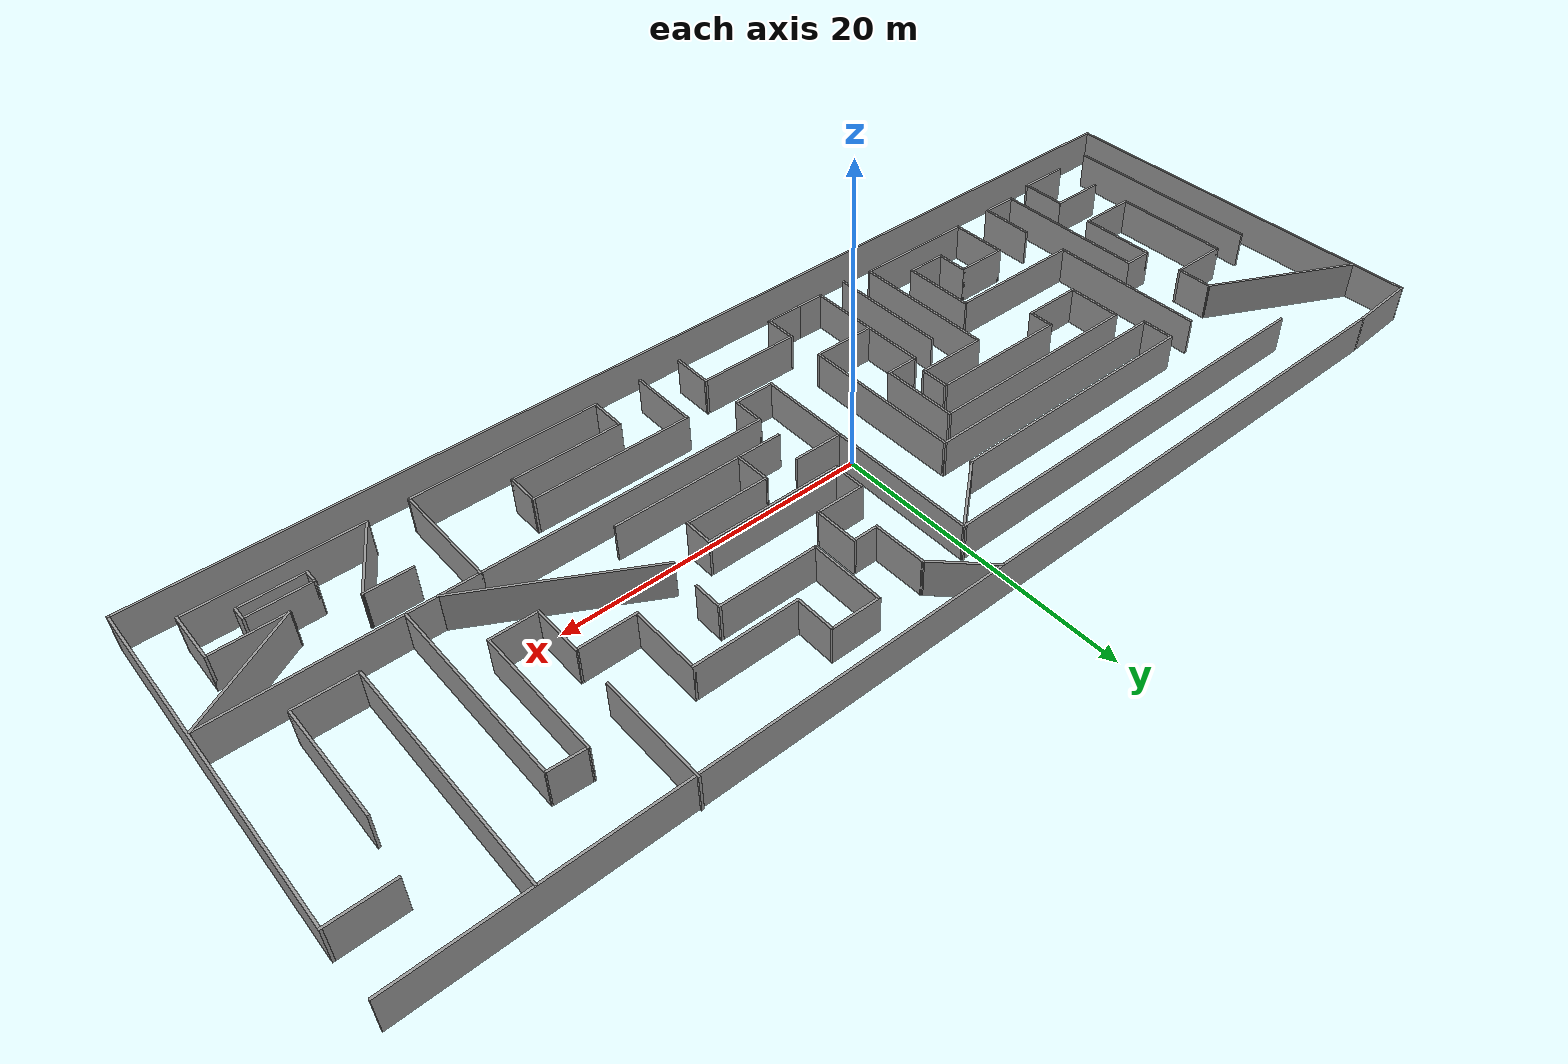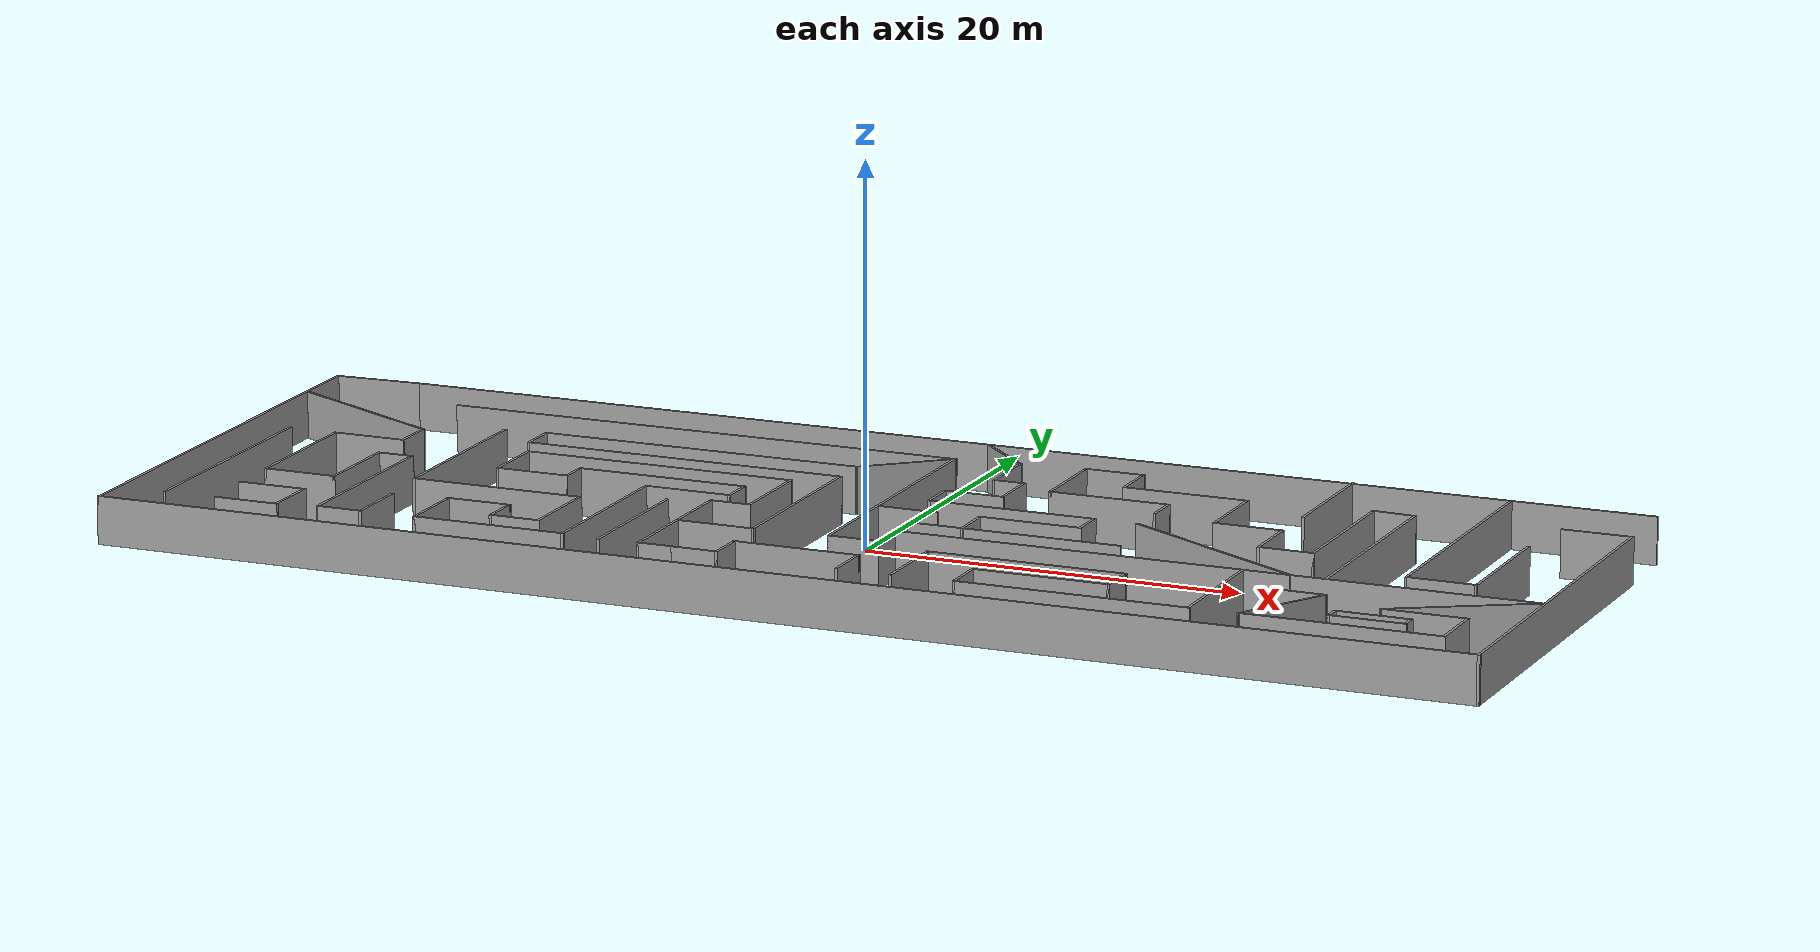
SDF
<?xml version='1.0'?>
<sdf version='1.6'>
  <model name='maze'>
    <pose frame=''>0.673756 -0.372053 0 0 -0 0</pose>
    <link name='Wall_101'>
      <collision name='Wall_101_Collision'>
        <geometry>
          <box>
            <size>0.15 0.15 2.5</size>
          </box>
        </geometry>
        <pose frame=''>0 0 1.25 0 -0 0</pose>
      </collision>
      <visual name='Wall_101_Visual'>
        <pose frame=''>0 0 1.25 0 -0 0</pose>
        <geometry>
          <box>
            <size>0.15 0.15 2.5</size>
          </box>
        </geometry>
        <material>
          <script>
            <uri>file://media/materials/scripts/gazebo.material</uri>
            <name>Gazebo/Grey</name>
          </script>
          <ambient>1 1 1 1</ambient>
        </material>
      </visual>
      <pose frame=''>27.6431 -9.00348 0 0 -0 0</pose>
    </link>
    <link name='Wall_108'>
      <collision name='Wall_108_Collision'>
        <geometry>
          <box>
            <size>4 0.15 2.5</size>
          </box>
        </geometry>
        <pose frame=''>0 0 1.25 0 -0 0</pose>
      </collision>
      <visual name='Wall_108_Visual'>
        <pose frame=''>0 0 1.25 0 -0 0</pose>
        <geometry>
          <box>
            <size>4 0.15 2.5</size>
          </box>
        </geometry>
        <material>
          <script>
            <uri>file://media/materials/scripts/gazebo.material</uri>
            <name>Gazebo/Grey</name>
          </script>
          <ambient>1 1 1 1</ambient>
        </material>
      </visual>
      <pose frame=''>29.5681 -9.00348 0 0 -0 0</pose>
    </link>
    <link name='Wall_109'>
      <collision name='Wall_109_Collision'>
        <geometry>
          <box>
            <size>1 0.15 2.5</size>
          </box>
        </geometry>
        <pose frame=''>0 0 1.25 0 -0 0</pose>
      </collision>
      <visual name='Wall_109_Visual'>
        <pose frame=''>0 0 1.25 0 -0 0</pose>
        <geometry>
          <box>
            <size>1 0.15 2.5</size>
          </box>
        </geometry>
        <material>
          <script>
            <uri>file://media/materials/scripts/gazebo.material</uri>
            <name>Gazebo/Grey</name>
          </script>
          <ambient>1 1 1 1</ambient>
        </material>
      </visual>
      <pose frame=''>31.4931 -9.42848 0 0 0 -1.5708</pose>
    </link>
    <link name='Wall_110'>
      <collision name='Wall_110_Collision'>
        <geometry>
          <box>
            <size>4 0.15 2.5</size>
          </box>
        </geometry>
        <pose frame=''>0 0 1.25 0 -0 0</pose>
      </collision>
      <visual name='Wall_110_Visual'>
        <pose frame=''>0 0 1.25 0 -0 0</pose>
        <geometry>
          <box>
            <size>4 0.15 2.5</size>
          </box>
        </geometry>
        <material>
          <script>
            <uri>file://media/materials/scripts/gazebo.material</uri>
            <name>Gazebo/Grey</name>
          </script>
          <ambient>1 1 1 1</ambient>
        </material>
      </visual>
      <pose frame=''>29.5681 -9.85348 0 0 -0 3.14159</pose>
    </link>
    <link name='Wall_111'>
      <collision name='Wall_111_Collision'>
        <geometry>
          <box>
            <size>1 0.15 2.5</size>
          </box>
        </geometry>
        <pose frame=''>0 0 1.25 0 -0 0</pose>
      </collision>
      <visual name='Wall_111_Visual'>
        <pose frame=''>0 0 1.25 0 -0 0</pose>
        <geometry>
          <box>
            <size>1 0.15 2.5</size>
          </box>
        </geometry>
        <material>
          <script>
            <uri>file://media/materials/scripts/gazebo.material</uri>
            <name>Gazebo/Grey</name>
          </script>
          <ambient>1 1 1 1</ambient>
        </material>
      </visual>
      <pose frame=''>27.6431 -9.42848 0 0 -0 1.5708</pose>
    </link>
    <link name='Wall_116'>
      <collision name='Wall_116_Collision'>
        <geometry>
          <box>
            <size>4.8415 0.15 2.5</size>
          </box>
        </geometry>
        <pose frame=''>0 0 1.25 0 -0 0</pose>
      </collision>
      <visual name='Wall_116_Visual'>
        <pose frame=''>0 0 1.25 0 -0 0</pose>
        <geometry>
          <box>
            <size>4.8415 0.15 2.5</size>
          </box>
        </geometry>
        <material>
          <script>
            <uri>file://media/materials/scripts/gazebo.material</uri>
            <name>Gazebo/Grey</name>
          </script>
          <ambient>1 1 1 1</ambient>
        </material>
      </visual>
      <pose frame=''>-34.0821 13.2535 0 0 -0 0.049384</pose>
    </link>
    <link name='Wall_12'>
      <collision name='Wall_12_Collision'>
        <geometry>
          <box>
            <size>28 0.15 2.5</size>
          </box>
        </geometry>
        <pose frame=''>0 0 1.25 0 -0 0</pose>
      </collision>
      <visual name='Wall_12_Visual'>
        <pose frame=''>0 0 1.25 0 -0 0</pose>
        <geometry>
          <box>
            <size>28 0.15 2.5</size>
          </box>
        </geometry>
        <material>
          <script>
            <uri>file://media/materials/scripts/gazebo.material</uri>
            <name>Gazebo/Grey</name>
          </script>
          <ambient>1 1 1 1</ambient>
        </material>
      </visual>
      <pose frame=''>-13.9482 10.0273 0 0 -0 0</pose>
    </link>
    <link name='Wall_124'>
      <collision name='Wall_124_Collision'>
        <geometry>
          <box>
            <size>3.64965 0.15 2.5</size>
          </box>
        </geometry>
        <pose frame=''>0 0 1.25 0 -0 0</pose>
      </collision>
      <visual name='Wall_124_Visual'>
        <pose frame=''>0 0 1.25 0 -0 0</pose>
        <geometry>
          <box>
            <size>3.64965 0.15 2.5</size>
          </box>
        </geometry>
        <material>
          <script>
            <uri>file://media/materials/scripts/gazebo.material</uri>
            <name>Gazebo/Grey</name>
          </script>
          <ambient>1 1 1 1</ambient>
        </material>
      </visual>
      <pose frame=''>3.52079 8.72354 0 0 0 -1.56012</pose>
    </link>
    <link name='Wall_125'>
      <collision name='Wall_125_Collision'>
        <geometry>
          <box>
            <size>1.75 0.15 2.5</size>
          </box>
        </geometry>
        <pose frame=''>0 0 1.25 0 -0 0</pose>
      </collision>
      <visual name='Wall_125_Visual'>
        <pose frame=''>0 0 1.25 0 -0 0</pose>
        <geometry>
          <box>
            <size>1.75 0.15 2.5</size>
          </box>
        </geometry>
        <material>
          <script>
            <uri>file://media/materials/scripts/gazebo.material</uri>
            <name>Gazebo/Grey</name>
          </script>
          <ambient>1 1 1 1</ambient>
        </material>
      </visual>
      <pose frame=''>4.33947 6.97382 0 0 -0 0</pose>
    </link>
    <link name='Wall_126'>
      <collision name='Wall_126_Collision'>
        <geometry>
          <box>
            <size>3 0.15 2.5</size>
          </box>
        </geometry>
        <pose frame=''>0 0 1.25 0 -0 0</pose>
      </collision>
      <visual name='Wall_126_Visual'>
        <pose frame=''>0 0 1.25 0 -0 0</pose>
        <geometry>
          <box>
            <size>3 0.15 2.5</size>
          </box>
        </geometry>
        <material>
          <script>
            <uri>file://media/materials/scripts/gazebo.material</uri>
            <name>Gazebo/Grey</name>
          </script>
          <ambient>1 1 1 1</ambient>
        </material>
      </visual>
      <pose frame=''>5.13947 5.54882 0 0 0 -1.5708</pose>
    </link>
    <link name='Wall_127'>
      <collision name='Wall_127_Collision'>
        <geometry>
          <box>
            <size>3.25 0.15 2.5</size>
          </box>
        </geometry>
        <pose frame=''>0 0 1.25 0 -0 0</pose>
      </collision>
      <visual name='Wall_127_Visual'>
        <pose frame=''>0 0 1.25 0 -0 0</pose>
        <geometry>
          <box>
            <size>3.25 0.15 2.5</size>
          </box>
        </geometry>
        <material>
          <script>
            <uri>file://media/materials/scripts/gazebo.material</uri>
            <name>Gazebo/Grey</name>
          </script>
          <ambient>1 1 1 1</ambient>
        </material>
      </visual>
      <pose frame=''>3.58947 4.12382 0 0 -0 3.14159</pose>
    </link>
    <link name='Wall_128'>
      <collision name='Wall_128_Collision'>
        <geometry>
          <box>
            <size>2.25 0.15 2.5</size>
          </box>
        </geometry>
        <pose frame=''>0 0 1.25 0 -0 0</pose>
      </collision>
      <visual name='Wall_128_Visual'>
        <pose frame=''>0 0 1.25 0 -0 0</pose>
        <geometry>
          <box>
            <size>2.25 0.15 2.5</size>
          </box>
        </geometry>
        <material>
          <script>
            <uri>file://media/materials/scripts/gazebo.material</uri>
            <name>Gazebo/Grey</name>
          </script>
          <ambient>1 1 1 1</ambient>
        </material>
      </visual>
      <pose frame=''>2.03947 3.07382 0 0 0 -1.5708</pose>
    </link>
    <link name='Wall_129'>
      <collision name='Wall_129_Collision'>
        <geometry>
          <box>
            <size>9 0.15 2.5</size>
          </box>
        </geometry>
        <pose frame=''>0 0 1.25 0 -0 0</pose>
      </collision>
      <visual name='Wall_129_Visual'>
        <pose frame=''>0 0 1.25 0 -0 0</pose>
        <geometry>
          <box>
            <size>9 0.15 2.5</size>
          </box>
        </geometry>
        <material>
          <script>
            <uri>file://media/materials/scripts/gazebo.material</uri>
            <name>Gazebo/Grey</name>
          </script>
          <ambient>1 1 1 1</ambient>
        </material>
      </visual>
      <pose frame=''>6.46447 2.02382 0 0 -0 0</pose>
    </link>
    <link name='Wall_13'>
      <collision name='Wall_13_Collision'>
        <geometry>
          <box>
            <size>5.35713 0.15 2.5</size>
          </box>
        </geometry>
        <pose frame=''>0 0 1.25 0 -0 0</pose>
      </collision>
      <visual name='Wall_13_Visual'>
        <pose frame=''>0 0 1.25 0 -0 0</pose>
        <geometry>
          <box>
            <size>5.35713 0.15 2.5</size>
          </box>
        </geometry>
        <material>
          <script>
            <uri>file://media/materials/scripts/gazebo.material</uri>
            <name>Gazebo/Grey</name>
          </script>
          <ambient>1 1 1 1</ambient>
        </material>
      </visual>
      <pose frame=''>-1.89938 8.3483 0 0 0 -2.44071</pose>
    </link>
    <link name='Wall_130'>
      <collision name='Wall_130_Collision'>
        <geometry>
          <box>
            <size>2 0.15 2.5</size>
          </box>
        </geometry>
        <pose frame=''>0 0 1.25 0 -0 0</pose>
      </collision>
      <visual name='Wall_130_Visual'>
        <pose frame=''>0 0 1.25 0 -0 0</pose>
        <geometry>
          <box>
            <size>2 0.15 2.5</size>
          </box>
        </geometry>
        <material>
          <script>
            <uri>file://media/materials/scripts/gazebo.material</uri>
            <name>Gazebo/Grey</name>
          </script>
          <ambient>1 1 1 1</ambient>
        </material>
      </visual>
      <pose frame=''>10.8895 1.09882 0 0 0 -1.5708</pose>
    </link>
    <link name='Wall_131'>
      <collision name='Wall_131_Collision'>
        <geometry>
          <box>
            <size>5.5 0.15 2.5</size>
          </box>
        </geometry>
        <pose frame=''>0 0 1.25 0 -0 0</pose>
      </collision>
      <visual name='Wall_131_Visual'>
        <pose frame=''>0 0 1.25 0 -0 0</pose>
        <geometry>
          <box>
            <size>5.5 0.15 2.5</size>
          </box>
        </geometry>
        <material>
          <script>
            <uri>file://media/materials/scripts/gazebo.material</uri>
            <name>Gazebo/Grey</name>
          </script>
          <ambient>1 1 1 1</ambient>
        </material>
      </visual>
      <pose frame=''>8.21447 0.173816 0 0 -0 3.14159</pose>
    </link>
    <link name='Wall_132'>
      <collision name='Wall_132_Collision'>
        <geometry>
          <box>
            <size>2.50126 0.15 2.5</size>
          </box>
        </geometry>
        <pose frame=''>0 0 1.25 0 -0 0</pose>
      </collision>
      <visual name='Wall_132_Visual'>
        <pose frame=''>0 0 1.25 0 -0 0</pose>
        <geometry>
          <box>
            <size>2.50126 0.15 2.5</size>
          </box>
        </geometry>
        <material>
          <script>
            <uri>file://media/materials/scripts/gazebo.material</uri>
            <name>Gazebo/Grey</name>
          </script>
          <ambient>1 1 1 1</ambient>
        </material>
      </visual>
      <pose frame=''>5.55875 -1.00118 0 0 0 -1.55439</pose>
    </link>
    <link name='Wall_133'>
      <collision name='Wall_133_Collision'>
        <geometry>
          <box>
            <size>8.46145 0.15 2.5</size>
          </box>
        </geometry>
        <pose frame=''>0 0 1.25 0 -0 0</pose>
      </collision>
      <visual name='Wall_133_Visual'>
        <pose frame=''>0 0 1.25 0 -0 0</pose>
        <geometry>
          <box>
            <size>8.46145 0.15 2.5</size>
          </box>
        </geometry>
        <material>
          <script>
            <uri>file://media/materials/scripts/gazebo.material</uri>
            <name>Gazebo/Grey</name>
          </script>
          <ambient>1 1 1 1</ambient>
        </material>
      </visual>
      <pose frame=''>9.73375 -2.17618 0 0 -0 0</pose>
    </link>
    <link name='Wall_14'>
      <collision name='Wall_14_Collision'>
        <geometry>
          <box>
            <size>17.5 0.15 2.5</size>
          </box>
        </geometry>
        <pose frame=''>0 0 1.25 0 -0 0</pose>
      </collision>
      <visual name='Wall_14_Visual'>
        <pose frame=''>0 0 1.25 0 -0 0</pose>
        <geometry>
          <box>
            <size>17.5 0.15 2.5</size>
          </box>
        </geometry>
        <material>
          <script>
            <uri>file://media/materials/scripts/gazebo.material</uri>
            <name>Gazebo/Grey</name>
          </script>
          <ambient>1 1 1 1</ambient>
        </material>
      </visual>
      <pose frame=''>-12.5642 6.66928 0 0 -0 3.14159</pose>
    </link>
    <link name='Wall_146'>
      <collision name='Wall_146_Collision'>
        <geometry>
          <box>
            <size>4.75 0.15 2.5</size>
          </box>
        </geometry>
        <pose frame=''>0 0 1.25 0 -0 0</pose>
      </collision>
      <visual name='Wall_146_Visual'>
        <pose frame=''>0 0 1.25 0 -0 0</pose>
        <geometry>
          <box>
            <size>4.75 0.15 2.5</size>
          </box>
        </geometry>
        <material>
          <script>
            <uri>file://media/materials/scripts/gazebo.material</uri>
            <name>Gazebo/Grey</name>
          </script>
          <ambient>1 1 1 1</ambient>
        </material>
      </visual>
      <pose frame=''>-7.98922 -8.58072 0 0 0 -1.5708</pose>
    </link>
    <link name='Wall_147'>
      <collision name='Wall_147_Collision'>
        <geometry>
          <box>
            <size>2 0.15 2.5</size>
          </box>
        </geometry>
        <pose frame=''>0 0 1.25 0 -0 0</pose>
      </collision>
      <visual name='Wall_147_Visual'>
        <pose frame=''>0 0 1.25 0 -0 0</pose>
        <geometry>
          <box>
            <size>2 0.15 2.5</size>
          </box>
        </geometry>
        <material>
          <script>
            <uri>file://media/materials/scripts/gazebo.material</uri>
            <name>Gazebo/Grey</name>
          </script>
          <ambient>1 1 1 1</ambient>
        </material>
      </visual>
      <pose frame=''>-7.06422 -10.8807 0 0 -0 0</pose>
    </link>
    <link name='Wall_148'>
      <collision name='Wall_148_Collision'>
        <geometry>
          <box>
            <size>2.5 0.15 2.5</size>
          </box>
        </geometry>
        <pose frame=''>0 0 1.25 0 -0 0</pose>
      </collision>
      <visual name='Wall_148_Visual'>
        <pose frame=''>0 0 1.25 0 -0 0</pose>
        <geometry>
          <box>
            <size>2.5 0.15 2.5</size>
          </box>
        </geometry>
        <material>
          <script>
            <uri>file://media/materials/scripts/gazebo.material</uri>
            <name>Gazebo/Grey</name>
          </script>
          <ambient>1 1 1 1</ambient>
        </material>
      </visual>
      <pose frame=''>-4.96422 -10.8807 0 0 -0 0</pose>
    </link>
    <link name='Wall_149'>
      <collision name='Wall_149_Collision'>
        <geometry>
          <box>
            <size>2.25 0.15 2.5</size>
          </box>
        </geometry>
        <pose frame=''>0 0 1.25 0 -0 0</pose>
      </collision>
      <visual name='Wall_149_Visual'>
        <pose frame=''>0 0 1.25 0 -0 0</pose>
        <geometry>
          <box>
            <size>2.25 0.15 2.5</size>
          </box>
        </geometry>
        <material>
          <script>
            <uri>file://media/materials/scripts/gazebo.material</uri>
            <name>Gazebo/Grey</name>
          </script>
          <ambient>1 1 1 1</ambient>
        </material>
      </visual>
      <pose frame=''>-3.78922 -9.83072 0 0 -0 1.5708</pose>
    </link>
    <link name='Wall_15'>
      <collision name='Wall_15_Collision'>
        <geometry>
          <box>
            <size>2.25 0.15 2.5</size>
          </box>
        </geometry>
        <pose frame=''>0 0 1.25 0 -0 0</pose>
      </collision>
      <visual name='Wall_15_Visual'>
        <pose frame=''>0 0 1.25 0 -0 0</pose>
        <geometry>
          <box>
            <size>2.25 0.15 2.5</size>
          </box>
        </geometry>
        <material>
          <script>
            <uri>file://media/materials/scripts/gazebo.material</uri>
            <name>Gazebo/Grey</name>
          </script>
          <ambient>1 1 1 1</ambient>
        </material>
      </visual>
      <pose frame=''>-21.2392 5.61928 0 0 0 -1.5708</pose>
    </link>
    <link name='Wall_150'>
      <collision name='Wall_150_Collision'>
        <geometry>
          <box>
            <size>6.75 0.15 2.5</size>
          </box>
        </geometry>
        <pose frame=''>0 0 1.25 0 -0 0</pose>
      </collision>
      <visual name='Wall_150_Visual'>
        <pose frame=''>0 0 1.25 0 -0 0</pose>
        <geometry>
          <box>
            <size>6.75 0.15 2.5</size>
          </box>
        </geometry>
        <material>
          <script>
            <uri>file://media/materials/scripts/gazebo.material</uri>
            <name>Gazebo/Grey</name>
          </script>
          <ambient>1 1 1 1</ambient>
        </material>
      </visual>
      <pose frame=''>-0.489216 -8.78072 0 0 -0 0</pose>
    </link>
    <link name='Wall_151'>
      <collision name='Wall_151_Collision'>
        <geometry>
          <box>
            <size>2.75 0.15 2.5</size>
          </box>
        </geometry>
        <pose frame=''>0 0 1.25 0 -0 0</pose>
      </collision>
      <visual name='Wall_151_Visual'>
        <pose frame=''>0 0 1.25 0 -0 0</pose>
        <geometry>
          <box>
            <size>2.75 0.15 2.5</size>
          </box>
        </geometry>
        <material>
          <script>
            <uri>file://media/materials/scripts/gazebo.material</uri>
            <name>Gazebo/Grey</name>
          </script>
          <ambient>1 1 1 1</ambient>
        </material>
      </visual>
      <pose frame=''>2.81078 -10.0807 0 0 0 -1.5708</pose>
    </link>
    <link name='Wall_153'>
      <collision name='Wall_153_Collision'>
        <geometry>
          <box>
            <size>8.25 0.15 2.5</size>
          </box>
        </geometry>
        <pose frame=''>0 0 1.25 0 -0 0</pose>
      </collision>
      <visual name='Wall_153_Visual'>
        <pose frame=''>0 0 1.25 0 -0 0</pose>
        <geometry>
          <box>
            <size>8.25 0.15 2.5</size>
          </box>
        </geometry>
        <material>
          <script>
            <uri>file://media/materials/scripts/gazebo.material</uri>
            <name>Gazebo/Grey</name>
          </script>
          <ambient>1 1 1 1</ambient>
        </material>
      </visual>
      <pose frame=''>-10.0893 -6.96963 0 0 0 -1.5708</pose>
    </link>
    <link name='Wall_156'>
      <collision name='Wall_156_Collision'>
        <geometry>
          <box>
            <size>10.75 0.15 2.5</size>
          </box>
        </geometry>
        <pose frame=''>0 0 1.25 0 -0 0</pose>
      </collision>
      <visual name='Wall_156_Visual'>
        <pose frame=''>0 0 1.25 0 -0 0</pose>
        <geometry>
          <box>
            <size>10.75 0.15 2.5</size>
          </box>
        </geometry>
        <material>
          <script>
            <uri>file://media/materials/scripts/gazebo.material</uri>
            <name>Gazebo/Grey</name>
          </script>
          <ambient>1 1 1 1</ambient>
        </material>
      </visual>
      <pose frame=''>-23.4764 1.11928 0 0 -0 1.5708</pose>
    </link>
    <link name='Wall_159'>
      <collision name='Wall_159_Collision'>
        <geometry>
          <box>
            <size>12 0.15 2.5</size>
          </box>
        </geometry>
        <pose frame=''>0 0 1.25 0 -0 0</pose>
      </collision>
      <visual name='Wall_159_Visual'>
        <pose frame=''>0 0 1.25 0 -0 0</pose>
        <geometry>
          <box>
            <size>12 0.15 2.5</size>
          </box>
        </geometry>
        <material>
          <script>
            <uri>file://media/materials/scripts/gazebo.material</uri>
            <name>Gazebo/Grey</name>
          </script>
          <ambient>1 1 1 1</ambient>
        </material>
      </visual>
      <pose frame=''>18.3267 -0.947598 0 0 0 -0.523599</pose>
    </link>
    <link name='Wall_16'>
      <collision name='Wall_16_Collision'>
        <geometry>
          <box>
            <size>17.5 0.15 2.5</size>
          </box>
        </geometry>
        <pose frame=''>0 0 1.25 0 -0 0</pose>
      </collision>
      <visual name='Wall_16_Visual'>
        <pose frame=''>0 0 1.25 0 -0 0</pose>
        <geometry>
          <box>
            <size>17.5 0.15 2.5</size>
          </box>
        </geometry>
        <material>
          <script>
            <uri>file://media/materials/scripts/gazebo.material</uri>
            <name>Gazebo/Grey</name>
          </script>
          <ambient>1 1 1 1</ambient>
        </material>
      </visual>
      <pose frame=''>-12.5642 4.56928 0 0 -0 0</pose>
    </link>
    <link name='Wall_165'>
      <collision name='Wall_165_Collision'>
        <geometry>
          <box>
            <size>3.25 0.15 2.5</size>
          </box>
        </geometry>
        <pose frame=''>0 0 1.25 0 -0 0</pose>
      </collision>
      <visual name='Wall_165_Visual'>
        <pose frame=''>0 0 1.25 0 -0 0</pose>
        <geometry>
          <box>
            <size>3.25 0.15 2.5</size>
          </box>
        </geometry>
        <material>
          <script>
            <uri>file://media/materials/scripts/gazebo.material</uri>
            <name>Gazebo/Grey</name>
          </script>
          <ambient>1 1 1 1</ambient>
        </material>
      </visual>
      <pose frame=''>1.67671 0.087351 0 0 -0 0</pose>
    </link>
    <link name='Wall_167'>
      <collision name='Wall_167_Collision'>
        <geometry>
          <box>
            <size>3 0.15 2.5</size>
          </box>
        </geometry>
        <pose frame=''>0 0 1.25 0 -0 0</pose>
      </collision>
      <visual name='Wall_167_Visual'>
        <pose frame=''>0 0 1.25 0 -0 0</pose>
        <geometry>
          <box>
            <size>3 0.15 2.5</size>
          </box>
        </geometry>
        <material>
          <script>
            <uri>file://media/materials/scripts/gazebo.material</uri>
            <name>Gazebo/Grey</name>
          </script>
          <ambient>1 1 1 1</ambient>
        </material>
      </visual>
      <pose frame=''>4.15302 -2.17618 0 0 -0 3.14159</pose>
    </link>
    <link name='Wall_17'>
      <collision name='Wall_17_Collision'>
        <geometry>
          <box>
            <size>11 0.15 2.5</size>
          </box>
        </geometry>
        <pose frame=''>0 0 1.25 0 -0 0</pose>
      </collision>
      <visual name='Wall_17_Visual'>
        <pose frame=''>0 0 1.25 0 -0 0</pose>
        <geometry>
          <box>
            <size>11 0.15 2.5</size>
          </box>
        </geometry>
        <material>
          <script>
            <uri>file://media/materials/scripts/gazebo.material</uri>
            <name>Gazebo/Grey</name>
          </script>
          <ambient>1 1 1 1</ambient>
        </material>
      </visual>
      <pose frame=''>-3.88922 -0.855718 0 0 0 -1.5708</pose>
    </link>
    <link name='Wall_18'>
      <collision name='Wall_18_Collision'>
        <geometry>
          <box>
            <size>4.25 0.15 2.5</size>
          </box>
        </geometry>
        <pose frame=''>0 0 1.25 0 -0 0</pose>
      </collision>
      <visual name='Wall_18_Visual'>
        <pose frame=''>0 0 1.25 0 -0 0</pose>
        <geometry>
          <box>
            <size>4.25 0.15 2.5</size>
          </box>
        </geometry>
        <material>
          <script>
            <uri>file://media/materials/scripts/gazebo.material</uri>
            <name>Gazebo/Grey</name>
          </script>
          <ambient>1 1 1 1</ambient>
        </material>
      </visual>
      <pose frame=''>-5.93922 -6.28072 0 0 -0 3.14159</pose>
    </link>
    <link name='Wall_183'>
      <collision name='Wall_183_Collision'>
        <geometry>
          <box>
            <size>12.75 0.15 2.5</size>
          </box>
        </geometry>
        <pose frame=''>0 0 1.25 0 -0 0</pose>
      </collision>
      <visual name='Wall_183_Visual'>
        <pose frame=''>0 0 1.25 0 -0 0</pose>
        <geometry>
          <box>
            <size>12.75 0.15 2.5</size>
          </box>
        </geometry>
        <material>
          <script>
            <uri>file://media/materials/scripts/gazebo.material</uri>
            <name>Gazebo/Grey</name>
          </script>
          <ambient>1 1 1 1</ambient>
        </material>
      </visual>
      <pose frame=''>25.3105 2.45804 0 0 -0 1.5708</pose>
    </link>
    <link name='Wall_185'>
      <collision name='Wall_185_Collision'>
        <geometry>
          <box>
            <size>15.5 0.15 2.5</size>
          </box>
        </geometry>
        <pose frame=''>0 0 1.25 0 -0 0</pose>
      </collision>
      <visual name='Wall_185_Visual'>
        <pose frame=''>0 0 1.25 0 -0 0</pose>
        <geometry>
          <box>
            <size>15.5 0.15 2.5</size>
          </box>
        </geometry>
        <material>
          <script>
            <uri>file://media/materials/scripts/gazebo.material</uri>
            <name>Gazebo/Grey</name>
          </script>
          <ambient>1 1 1 1</ambient>
        </material>
      </visual>
      <pose frame=''>28.7569 5.64093 0 0 0 -1.5708</pose>
    </link>
    <link name='Wall_186'>
      <collision name='Wall_186_Collision'>
        <geometry>
          <box>
            <size>3.75 0.15 2.5</size>
          </box>
        </geometry>
        <pose frame=''>0 0 1.25 0 -0 0</pose>
      </collision>
      <visual name='Wall_186_Visual'>
        <pose frame=''>0 0 1.25 0 -0 0</pose>
        <geometry>
          <box>
            <size>3.75 0.15 2.5</size>
          </box>
        </geometry>
        <material>
          <script>
            <uri>file://media/materials/scripts/gazebo.material</uri>
            <name>Gazebo/Grey</name>
          </script>
          <ambient>1 1 1 1</ambient>
        </material>
      </visual>
      <pose frame=''>30.5569 -2.0526 0 0 0 -0.010294</pose>
    </link>
    <link name='Wall_189'>
      <collision name='Wall_189_Collision'>
        <geometry>
          <box>
            <size>3.75 0.15 2.5</size>
          </box>
        </geometry>
        <pose frame=''>0 0 1.25 0 -0 0</pose>
      </collision>
      <visual name='Wall_189_Visual'>
        <pose frame=''>0 0 1.25 0 -0 0</pose>
        <geometry>
          <box>
            <size>3.75 0.15 2.5</size>
          </box>
        </geometry>
        <material>
          <script>
            <uri>file://media/materials/scripts/gazebo.material</uri>
            <name>Gazebo/Grey</name>
          </script>
          <ambient>1 1 1 1</ambient>
        </material>
      </visual>
      <pose frame=''>34.6633 9.24997 0 0 -0 3.14159</pose>
    </link>
    <link name='Wall_19'>
      <collision name='Wall_19_Collision'>
        <geometry>
          <box>
            <size>4.25 0.15 2.5</size>
          </box>
        </geometry>
        <pose frame=''>0 0 1.25 0 -0 0</pose>
      </collision>
      <visual name='Wall_19_Visual'>
        <pose frame=''>0 0 1.25 0 -0 0</pose>
        <geometry>
          <box>
            <size>4.25 0.15 2.5</size>
          </box>
        </geometry>
        <material>
          <script>
            <uri>file://media/materials/scripts/gazebo.material</uri>
            <name>Gazebo/Grey</name>
          </script>
          <ambient>1 1 1 1</ambient>
        </material>
      </visual>
      <pose frame=''>-7.98922 -4.23072 0 0 -0 1.5708</pose>
    </link>
    <link name='Wall_191'>
      <collision name='Wall_191_Collision'>
        <geometry>
          <box>
            <size>7.75 0.15 2.5</size>
          </box>
        </geometry>
        <pose frame=''>0 0 1.25 0 -0 0</pose>
      </collision>
      <visual name='Wall_191_Visual'>
        <pose frame=''>0 0 1.25 0 -0 0</pose>
        <geometry>
          <box>
            <size>7.75 0.15 2.5</size>
          </box>
        </geometry>
        <material>
          <script>
            <uri>file://media/materials/scripts/gazebo.material</uri>
            <name>Gazebo/Grey</name>
          </script>
          <ambient>1 1 1 1</ambient>
        </material>
      </visual>
      <pose frame=''>32.3569 1.72887 0 0 -0 1.5708</pose>
    </link>
    <link name='Wall_195'>
      <collision name='Wall_195_Collision'>
        <geometry>
          <box>
            <size>4.25 0.15 2.5</size>
          </box>
        </geometry>
        <pose frame=''>0 0 1.25 0 -0 0</pose>
      </collision>
      <visual name='Wall_195_Visual'>
        <pose frame=''>0 0 1.25 0 -0 0</pose>
        <geometry>
          <box>
            <size>4.25 0.15 2.5</size>
          </box>
        </geometry>
        <material>
          <script>
            <uri>file://media/materials/scripts/gazebo.material</uri>
            <name>Gazebo/Grey</name>
          </script>
          <ambient>1 1 1 1</ambient>
        </material>
      </visual>
      <pose frame=''>2.05254 11.8855 0 0 -0 2.35619</pose>
    </link>
    <link name='Wall_197'>
      <collision name='Wall_197_Collision'>
        <geometry>
          <box>
            <size>2 0.15 2.5</size>
          </box>
        </geometry>
        <pose frame=''>0 0 1.25 0 -0 0</pose>
      </collision>
      <visual name='Wall_197_Visual'>
        <pose frame=''>0 0 1.25 0 -0 0</pose>
        <geometry>
          <box>
            <size>2 0.15 2.5</size>
          </box>
        </geometry>
        <material>
          <script>
            <uri>file://media/materials/scripts/gazebo.material</uri>
            <name>Gazebo/Grey</name>
          </script>
          <ambient>1 1 1 1</ambient>
        </material>
      </visual>
      <pose frame=''>13.2968 5.06398 0 0 -0 1.5708</pose>
    </link>
    <link name='Wall_198'>
      <collision name='Wall_198_Collision'>
        <geometry>
          <box>
            <size>6.5 0.15 2.5</size>
          </box>
        </geometry>
        <pose frame=''>0 0 1.25 0 -0 0</pose>
      </collision>
      <visual name='Wall_198_Visual'>
        <pose frame=''>0 0 1.25 0 -0 0</pose>
        <geometry>
          <box>
            <size>6.5 0.15 2.5</size>
          </box>
        </geometry>
        <material>
          <script>
            <uri>file://media/materials/scripts/gazebo.material</uri>
            <name>Gazebo/Grey</name>
          </script>
          <ambient>1 1 1 1</ambient>
        </material>
      </visual>
      <pose frame=''>10.1218 5.98898 0 0 -0 3.14159</pose>
    </link>
    <link name='Wall_199'>
      <collision name='Wall_199_Collision'>
        <geometry>
          <box>
            <size>5 0.15 2.5</size>
          </box>
        </geometry>
        <pose frame=''>0 0 1.25 0 -0 0</pose>
      </collision>
      <visual name='Wall_199_Visual'>
        <pose frame=''>0 0 1.25 0 -0 0</pose>
        <geometry>
          <box>
            <size>5 0.15 2.5</size>
          </box>
        </geometry>
        <material>
          <script>
            <uri>file://media/materials/scripts/gazebo.material</uri>
            <name>Gazebo/Grey</name>
          </script>
          <ambient>1 1 1 1</ambient>
        </material>
      </visual>
      <pose frame=''>6.94681 8.41398 0 0 -0 1.5708</pose>
    </link>
    <link name='Wall_20'>
      <collision name='Wall_20_Collision'>
        <geometry>
          <box>
            <size>2.25 0.15 2.5</size>
          </box>
        </geometry>
        <pose frame=''>0 0 1.25 0 -0 0</pose>
      </collision>
      <visual name='Wall_20_Visual'>
        <pose frame=''>0 0 1.25 0 -0 0</pose>
        <geometry>
          <box>
            <size>2.25 0.15 2.5</size>
          </box>
        </geometry>
        <material>
          <script>
            <uri>file://media/materials/scripts/gazebo.material</uri>
            <name>Gazebo/Grey</name>
          </script>
          <ambient>1 1 1 1</ambient>
        </material>
      </visual>
      <pose frame=''>-6.93922 -2.18072 0 0 -0 0</pose>
    </link>
    <link name='Wall_200'>
      <collision name='Wall_200_Collision'>
        <geometry>
          <box>
            <size>3.25 0.15 2.5</size>
          </box>
        </geometry>
        <pose frame=''>0 0 1.25 0 -0 0</pose>
      </collision>
      <visual name='Wall_200_Visual'>
        <pose frame=''>0 0 1.25 0 -0 0</pose>
        <geometry>
          <box>
            <size>3.25 0.15 2.5</size>
          </box>
        </geometry>
        <material>
          <script>
            <uri>file://media/materials/scripts/gazebo.material</uri>
            <name>Gazebo/Grey</name>
          </script>
          <ambient>1 1 1 1</ambient>
        </material>
      </visual>
      <pose frame=''>8.49681 10.839 0 0 -0 0</pose>
    </link>
    <link name='Wall_201'>
      <collision name='Wall_201_Collision'>
        <geometry>
          <box>
            <size>2.75 0.15 2.5</size>
          </box>
        </geometry>
        <pose frame=''>0 0 1.25 0 -0 0</pose>
      </collision>
      <visual name='Wall_201_Visual'>
        <pose frame=''>0 0 1.25 0 -0 0</pose>
        <geometry>
          <box>
            <size>2.75 0.15 2.5</size>
          </box>
        </geometry>
        <material>
          <script>
            <uri>file://media/materials/scripts/gazebo.material</uri>
            <name>Gazebo/Grey</name>
          </script>
          <ambient>1 1 1 1</ambient>
        </material>
      </visual>
      <pose frame=''>10.0468 9.53898 0 0 0 -1.5708</pose>
    </link>
    <link name='Wall_202'>
      <collision name='Wall_202_Collision'>
        <geometry>
          <box>
            <size>6.75 0.15 2.5</size>
          </box>
        </geometry>
        <pose frame=''>0 0 1.25 0 -0 0</pose>
      </collision>
      <visual name='Wall_202_Visual'>
        <pose frame=''>0 0 1.25 0 -0 0</pose>
        <geometry>
          <box>
            <size>6.75 0.15 2.5</size>
          </box>
        </geometry>
        <material>
          <script>
            <uri>file://media/materials/scripts/gazebo.material</uri>
            <name>Gazebo/Grey</name>
          </script>
          <ambient>1 1 1 1</ambient>
        </material>
      </visual>
      <pose frame=''>13.3468 8.23898 0 0 -0 0</pose>
    </link>
    <link name='Wall_203'>
      <collision name='Wall_203_Collision'>
        <geometry>
          <box>
            <size>4.75 0.15 2.5</size>
          </box>
        </geometry>
        <pose frame=''>0 0 1.25 0 -0 0</pose>
      </collision>
      <visual name='Wall_203_Visual'>
        <pose frame=''>0 0 1.25 0 -0 0</pose>
        <geometry>
          <box>
            <size>4.75 0.15 2.5</size>
          </box>
        </geometry>
        <material>
          <script>
            <uri>file://media/materials/scripts/gazebo.material</uri>
            <name>Gazebo/Grey</name>
          </script>
          <ambient>1 1 1 1</ambient>
        </material>
      </visual>
      <pose frame=''>16.6468 5.93898 0 0 0 -1.5708</pose>
    </link>
    <link name='Wall_204'>
      <collision name='Wall_204_Collision'>
        <geometry>
          <box>
            <size>3.75 0.15 2.5</size>
          </box>
        </geometry>
        <pose frame=''>0 0 1.25 0 -0 0</pose>
      </collision>
      <visual name='Wall_204_Visual'>
        <pose frame=''>0 0 1.25 0 -0 0</pose>
        <geometry>
          <box>
            <size>3.75 0.15 2.5</size>
          </box>
        </geometry>
        <material>
          <script>
            <uri>file://media/materials/scripts/gazebo.material</uri>
            <name>Gazebo/Grey</name>
          </script>
          <ambient>1 1 1 1</ambient>
        </material>
      </visual>
      <pose frame=''>18.4468 3.63898 0 0 -0 0</pose>
    </link>
    <link name='Wall_205'>
      <collision name='Wall_205_Collision'>
        <geometry>
          <box>
            <size>3.5 0.15 2.5</size>
          </box>
        </geometry>
        <pose frame=''>0 0 1.25 0 -0 0</pose>
      </collision>
      <visual name='Wall_205_Visual'>
        <pose frame=''>0 0 1.25 0 -0 0</pose>
        <geometry>
          <box>
            <size>3.5 0.15 2.5</size>
          </box>
        </geometry>
        <material>
          <script>
            <uri>file://media/materials/scripts/gazebo.material</uri>
            <name>Gazebo/Grey</name>
          </script>
          <ambient>1 1 1 1</ambient>
        </material>
      </visual>
      <pose frame=''>20.2468 1.96398 0 0 0 -1.5708</pose>
    </link>
    <link name='Wall_206'>
      <collision name='Wall_206_Collision'>
        <geometry>
          <box>
            <size>3 0.15 2.5</size>
          </box>
        </geometry>
        <pose frame=''>0 0 1.25 0 -0 0</pose>
      </collision>
      <visual name='Wall_206_Visual'>
        <pose frame=''>0 0 1.25 0 -0 0</pose>
        <geometry>
          <box>
            <size>3 0.15 2.5</size>
          </box>
        </geometry>
        <material>
          <script>
            <uri>file://media/materials/scripts/gazebo.material</uri>
            <name>Gazebo/Grey</name>
          </script>
          <ambient>1 1 1 1</ambient>
        </material>
      </visual>
      <pose frame=''>21.6718 0.288983 0 0 -0 0</pose>
    </link>
    <link name='Wall_207'>
      <collision name='Wall_207_Collision'>
        <geometry>
          <box>
            <size>8.75 0.15 2.5</size>
          </box>
        </geometry>
        <pose frame=''>0 0 1.25 0 -0 0</pose>
      </collision>
      <visual name='Wall_207_Visual'>
        <pose frame=''>0 0 1.25 0 -0 0</pose>
        <geometry>
          <box>
            <size>8.75 0.15 2.5</size>
          </box>
        </geometry>
        <material>
          <script>
            <uri>file://media/materials/scripts/gazebo.material</uri>
            <name>Gazebo/Grey</name>
          </script>
          <ambient>1 1 1 1</ambient>
        </material>
      </visual>
      <pose frame=''>23.0968 4.58898 0 0 -0 1.5708</pose>
    </link>
    <link name='Wall_21'>
      <collision name='Wall_21_Collision'>
        <geometry>
          <box>
            <size>5.25 0.15 2.5</size>
          </box>
        </geometry>
        <pose frame=''>0 0 1.25 0 -0 0</pose>
      </collision>
      <visual name='Wall_21_Visual'>
        <pose frame=''>0 0 1.25 0 -0 0</pose>
        <geometry>
          <box>
            <size>5.25 0.15 2.5</size>
          </box>
        </geometry>
        <material>
          <script>
            <uri>file://media/materials/scripts/gazebo.material</uri>
            <name>Gazebo/Grey</name>
          </script>
          <ambient>1 1 1 1</ambient>
        </material>
      </visual>
      <pose frame=''>-5.88922 0.369282 0 0 -0 1.5708</pose>
    </link>
    <link name='Wall_211'>
      <collision name='Wall_211_Collision'>
        <geometry>
          <box>
            <size>2.36759 0.15 2.5</size>
          </box>
        </geometry>
        <pose frame=''>0 0 1.25 0 -0 0</pose>
      </collision>
      <visual name='Wall_211_Visual'>
        <pose frame=''>0 0 1.25 0 -0 0</pose>
        <geometry>
          <box>
            <size>2.36759 0.15 2.5</size>
          </box>
        </geometry>
        <material>
          <script>
            <uri>file://media/materials/scripts/gazebo.material</uri>
            <name>Gazebo/Grey</name>
          </script>
          <ambient>1 1 1 1</ambient>
        </material>
      </visual>
      <pose frame=''>24.2037 8.82351 0 0 0 -0.059081</pose>
    </link>
    <link name='Wall_213'>
      <collision name='Wall_213_Collision'>
        <geometry>
          <box>
            <size>7.25 0.15 2.5</size>
          </box>
        </geometry>
        <pose frame=''>0 0 1.25 0 -0 0</pose>
      </collision>
      <visual name='Wall_213_Visual'>
        <pose frame=''>0 0 1.25 0 -0 0</pose>
        <geometry>
          <box>
            <size>7.25 0.15 2.5</size>
          </box>
        </geometry>
        <material>
          <script>
            <uri>file://media/materials/scripts/gazebo.material</uri>
            <name>Gazebo/Grey</name>
          </script>
          <ambient>1 1 1 1</ambient>
        </material>
      </visual>
      <pose frame=''>20.3052 9.93734 0 0 0 -1.5708</pose>
    </link>
    <link name='Wall_22'>
      <collision name='Wall_22_Collision'>
        <geometry>
          <box>
            <size>14.75 0.15 2.5</size>
          </box>
        </geometry>
        <pose frame=''>0 0 1.25 0 -0 0</pose>
      </collision>
      <visual name='Wall_22_Visual'>
        <pose frame=''>0 0 1.25 0 -0 0</pose>
        <geometry>
          <box>
            <size>14.75 0.15 2.5</size>
          </box>
        </geometry>
        <material>
          <script>
            <uri>file://media/materials/scripts/gazebo.material</uri>
            <name>Gazebo/Grey</name>
          </script>
          <ambient>1 1 1 1</ambient>
        </material>
      </visual>
      <pose frame=''>-13.1892 2.91928 0 0 -0 3.14159</pose>
    </link>
    <link name='Wall_23'>
      <collision name='Wall_23_Collision'>
        <geometry>
          <box>
            <size>3.75 0.15 2.5</size>
          </box>
        </geometry>
        <pose frame=''>0 0 1.25 0 -0 0</pose>
      </collision>
      <visual name='Wall_23_Visual'>
        <pose frame=''>0 0 1.25 0 -0 0</pose>
        <geometry>
          <box>
            <size>3.75 0.15 2.5</size>
          </box>
        </geometry>
        <material>
          <script>
            <uri>file://media/materials/scripts/gazebo.material</uri>
            <name>Gazebo/Grey</name>
          </script>
          <ambient>1 1 1 1</ambient>
        </material>
      </visual>
      <pose frame=''>-20.4892 1.11928 0 0 0 -1.5708</pose>
    </link>
    <link name='Wall_24'>
      <collision name='Wall_24_Collision'>
        <geometry>
          <box>
            <size>4 0.15 2.5</size>
          </box>
        </geometry>
        <pose frame=''>0 0 1.25 0 -0 0</pose>
      </collision>
      <visual name='Wall_24_Visual'>
        <pose frame=''>0 0 1.25 0 -0 0</pose>
        <geometry>
          <box>
            <size>4 0.15 2.5</size>
          </box>
        </geometry>
        <material>
          <script>
            <uri>file://media/materials/scripts/gazebo.material</uri>
            <name>Gazebo/Grey</name>
          </script>
          <ambient>1 1 1 1</ambient>
        </material>
      </visual>
      <pose frame=''>-18.5642 -0.680718 0 0 -0 0</pose>
    </link>
    <link name='Wall_25'>
      <collision name='Wall_25_Collision'>
        <geometry>
          <box>
            <size>1.75 0.15 2.5</size>
          </box>
        </geometry>
        <pose frame=''>0 0 1.25 0 -0 0</pose>
      </collision>
      <visual name='Wall_25_Visual'>
        <pose frame=''>0 0 1.25 0 -0 0</pose>
        <geometry>
          <box>
            <size>1.75 0.15 2.5</size>
          </box>
        </geometry>
        <material>
          <script>
            <uri>file://media/materials/scripts/gazebo.material</uri>
            <name>Gazebo/Grey</name>
          </script>
          <ambient>1 1 1 1</ambient>
        </material>
      </visual>
      <pose frame=''>-16.6392 0.119282 0 0 -0 1.5708</pose>
    </link>
    <link name='Wall_26'>
      <collision name='Wall_26_Collision'>
        <geometry>
          <box>
            <size>9.25 0.15 2.5</size>
          </box>
        </geometry>
        <pose frame=''>0 0 1.25 0 -0 0</pose>
      </collision>
      <visual name='Wall_26_Visual'>
        <pose frame=''>0 0 1.25 0 -0 0</pose>
        <geometry>
          <box>
            <size>9.25 0.15 2.5</size>
          </box>
        </geometry>
        <material>
          <script>
            <uri>file://media/materials/scripts/gazebo.material</uri>
            <name>Gazebo/Grey</name>
          </script>
          <ambient>1 1 1 1</ambient>
        </material>
      </visual>
      <pose frame=''>-12.0892 0.919282 0 0 -0 0</pose>
    </link>
    <link name='Wall_27'>
      <collision name='Wall_27_Collision'>
        <geometry>
          <box>
            <size>2 0.15 2.5</size>
          </box>
        </geometry>
        <pose frame=''>0 0 1.25 0 -0 0</pose>
      </collision>
      <visual name='Wall_27_Visual'>
        <pose frame=''>0 0 1.25 0 -0 0</pose>
        <geometry>
          <box>
            <size>2 0.15 2.5</size>
          </box>
        </geometry>
        <material>
          <script>
            <uri>file://media/materials/scripts/gazebo.material</uri>
            <name>Gazebo/Grey</name>
          </script>
          <ambient>1 1 1 1</ambient>
        </material>
      </visual>
      <pose frame=''>-7.53922 -0.005718 0 0 0 -1.5708</pose>
    </link>
    <link name='Wall_28'>
      <collision name='Wall_28_Collision'>
        <geometry>
          <box>
            <size>4.75 0.15 2.5</size>
          </box>
        </geometry>
        <pose frame=''>0 0 1.25 0 -0 0</pose>
      </collision>
      <visual name='Wall_28_Visual'>
        <pose frame=''>0 0 1.25 0 -0 0</pose>
        <geometry>
          <box>
            <size>4.75 0.15 2.5</size>
          </box>
        </geometry>
        <material>
          <script>
            <uri>file://media/materials/scripts/gazebo.material</uri>
            <name>Gazebo/Grey</name>
          </script>
          <ambient>1 1 1 1</ambient>
        </material>
      </visual>
      <pose frame=''>-9.83922 -0.930718 0 0 -0 3.14159</pose>
    </link>
    <link name='Wall_29'>
      <collision name='Wall_29_Collision'>
        <geometry>
          <box>
            <size>10 0.15 2.5</size>
          </box>
        </geometry>
        <pose frame=''>0 0 1.25 0 -0 0</pose>
      </collision>
      <visual name='Wall_29_Visual'>
        <pose frame=''>0 0 1.25 0 -0 0</pose>
        <geometry>
          <box>
            <size>10 0.15 2.5</size>
          </box>
        </geometry>
        <material>
          <script>
            <uri>file://media/materials/scripts/gazebo.material</uri>
            <name>Gazebo/Grey</name>
          </script>
          <ambient>1 1 1 1</ambient>
        </material>
      </visual>
      <pose frame=''>-12.1392 -5.85572 0 0 0 -1.5708</pose>
    </link>
    <link name='Wall_30'>
      <collision name='Wall_30_Collision'>
        <geometry>
          <box>
            <size>8.25 0.15 2.5</size>
          </box>
        </geometry>
        <pose frame=''>0 0 1.25 0 -0 0</pose>
      </collision>
      <visual name='Wall_30_Visual'>
        <pose frame=''>0 0 1.25 0 -0 0</pose>
        <geometry>
          <box>
            <size>8.25 0.15 2.5</size>
          </box>
        </geometry>
        <material>
          <script>
            <uri>file://media/materials/scripts/gazebo.material</uri>
            <name>Gazebo/Grey</name>
          </script>
          <ambient>1 1 1 1</ambient>
        </material>
      </visual>
      <pose frame=''>-16.1892 -10.7807 0 0 -0 3.14159</pose>
    </link>
    <link name='Wall_31'>
      <collision name='Wall_31_Collision'>
        <geometry>
          <box>
            <size>4 0.15 2.5</size>
          </box>
        </geometry>
        <pose frame=''>0 0 1.25 0 -0 0</pose>
      </collision>
      <visual name='Wall_31_Visual'>
        <pose frame=''>0 0 1.25 0 -0 0</pose>
        <geometry>
          <box>
            <size>4 0.15 2.5</size>
          </box>
        </geometry>
        <material>
          <script>
            <uri>file://media/materials/scripts/gazebo.material</uri>
            <name>Gazebo/Grey</name>
          </script>
          <ambient>1 1 1 1</ambient>
        </material>
      </visual>
      <pose frame=''>-20.2392 -8.85572 0 0 -0 1.5708</pose>
    </link>
    <link name='Wall_32'>
      <collision name='Wall_32_Collision'>
        <geometry>
          <box>
            <size>3.5 0.15 2.5</size>
          </box>
        </geometry>
        <pose frame=''>0 0 1.25 0 -0 0</pose>
      </collision>
      <visual name='Wall_32_Visual'>
        <pose frame=''>0 0 1.25 0 -0 0</pose>
        <geometry>
          <box>
            <size>3.5 0.15 2.5</size>
          </box>
        </geometry>
        <material>
          <script>
            <uri>file://media/materials/scripts/gazebo.material</uri>
            <name>Gazebo/Grey</name>
          </script>
          <ambient>1 1 1 1</ambient>
        </material>
      </visual>
      <pose frame=''>-18.5642 -6.93072 0 0 -0 0</pose>
    </link>
    <link name='Wall_33'>
      <collision name='Wall_33_Collision'>
        <geometry>
          <box>
            <size>2.25 0.15 2.5</size>
          </box>
        </geometry>
        <pose frame=''>0 0 1.25 0 -0 0</pose>
      </collision>
      <visual name='Wall_33_Visual'>
        <pose frame=''>0 0 1.25 0 -0 0</pose>
        <geometry>
          <box>
            <size>2.25 0.15 2.5</size>
          </box>
        </geometry>
        <material>
          <script>
            <uri>file://media/materials/scripts/gazebo.material</uri>
            <name>Gazebo/Grey</name>
          </script>
          <ambient>1 1 1 1</ambient>
        </material>
      </visual>
      <pose frame=''>-16.8892 -7.98072 0 0 0 -1.5708</pose>
    </link>
    <link name='Wall_34'>
      <collision name='Wall_34_Collision'>
        <geometry>
          <box>
            <size>2.75 0.15 2.5</size>
          </box>
        </geometry>
        <pose frame=''>0 0 1.25 0 -0 0</pose>
      </collision>
      <visual name='Wall_34_Visual'>
        <pose frame=''>0 0 1.25 0 -0 0</pose>
        <geometry>
          <box>
            <size>2.75 0.15 2.5</size>
          </box>
        </geometry>
        <material>
          <script>
            <uri>file://media/materials/scripts/gazebo.material</uri>
            <name>Gazebo/Grey</name>
          </script>
          <ambient>1 1 1 1</ambient>
        </material>
      </visual>
      <pose frame=''>-15.5892 -9.03072 0 0 -0 0</pose>
    </link>
    <link name='Wall_35'>
      <collision name='Wall_35_Collision'>
        <geometry>
          <box>
            <size>5 0.15 2.5</size>
          </box>
        </geometry>
        <pose frame=''>0 0 1.25 0 -0 0</pose>
      </collision>
      <visual name='Wall_35_Visual'>
        <pose frame=''>0 0 1.25 0 -0 0</pose>
        <geometry>
          <box>
            <size>5 0.15 2.5</size>
          </box>
        </geometry>
        <material>
          <script>
            <uri>file://media/materials/scripts/gazebo.material</uri>
            <name>Gazebo/Grey</name>
          </script>
          <ambient>1 1 1 1</ambient>
        </material>
      </visual>
      <pose frame=''>-14.2892 -6.60572 0 0 -0 1.5708</pose>
    </link>
    <link name='Wall_36'>
      <collision name='Wall_36_Collision'>
        <geometry>
          <box>
            <size>9.33717 0.15 2.5</size>
          </box>
        </geometry>
        <pose frame=''>0 0 1.25 0 -0 0</pose>
      </collision>
      <visual name='Wall_36_Visual'>
        <pose frame=''>0 0 1.25 0 -0 0</pose>
        <geometry>
          <box>
            <size>9.33717 0.15 2.5</size>
          </box>
        </geometry>
        <material>
          <script>
            <uri>file://media/materials/scripts/gazebo.material</uri>
            <name>Gazebo/Grey</name>
          </script>
          <ambient>1 1 1 1</ambient>
        </material>
      </visual>
      <pose frame=''>-18.8828 -4.18072 0 0 -0 3.14159</pose>
    </link>
    <link name='Wall_40'>
      <collision name='Wall_40_Collision'>
        <geometry>
          <box>
            <size>10.2783 0.15 2.5</size>
          </box>
        </geometry>
        <pose frame=''>0 0 1.25 0 -0 0</pose>
      </collision>
      <visual name='Wall_40_Visual'>
        <pose frame=''>0 0 1.25 0 -0 0</pose>
        <geometry>
          <box>
            <size>10.2783 0.15 2.5</size>
          </box>
        </geometry>
        <material>
          <script>
            <uri>file://media/materials/scripts/gazebo.material</uri>
            <name>Gazebo/Grey</name>
          </script>
          <ambient>1 1 1 1</ambient>
        </material>
      </visual>
      <pose frame=''>-31.8772 7.16528 0 0 0 -0.481664</pose>
    </link>
    <link name='Wall_41'>
      <collision name='Wall_41_Collision'>
        <geometry>
          <box>
            <size>2.5 0.15 2.5</size>
          </box>
        </geometry>
        <pose frame=''>0 0 1.25 0 -0 0</pose>
      </collision>
      <visual name='Wall_41_Visual'>
        <pose frame=''>0 0 1.25 0 -0 0</pose>
        <geometry>
          <box>
            <size>2.5 0.15 2.5</size>
          </box>
        </geometry>
        <material>
          <script>
            <uri>file://media/materials/scripts/gazebo.material</uri>
            <name>Gazebo/Grey</name>
          </script>
          <ambient>1 1 1 1</ambient>
        </material>
      </visual>
      <pose frame=''>-27.3892 3.64428 0 0 0 -1.5708</pose>
    </link>
    <link name='Wall_42'>
      <collision name='Wall_42_Collision'>
        <geometry>
          <box>
            <size>4 0.15 2.5</size>
          </box>
        </geometry>
        <pose frame=''>0 0 1.25 0 -0 0</pose>
      </collision>
      <visual name='Wall_42_Visual'>
        <pose frame=''>0 0 1.25 0 -0 0</pose>
        <geometry>
          <box>
            <size>4 0.15 2.5</size>
          </box>
        </geometry>
        <material>
          <script>
            <uri>file://media/materials/scripts/gazebo.material</uri>
            <name>Gazebo/Grey</name>
          </script>
          <ambient>1 1 1 1</ambient>
        </material>
      </visual>
      <pose frame=''>-29.3142 2.46928 0 0 -0 3.14159</pose>
    </link>
    <link name='Wall_43'>
      <collision name='Wall_43_Collision'>
        <geometry>
          <box>
            <size>8 0.15 2.5</size>
          </box>
        </geometry>
        <pose frame=''>0 0 1.25 0 -0 0</pose>
      </collision>
      <visual name='Wall_43_Visual'>
        <pose frame=''>0 0 1.25 0 -0 0</pose>
        <geometry>
          <box>
            <size>8 0.15 2.5</size>
          </box>
        </geometry>
        <material>
          <script>
            <uri>file://media/materials/scripts/gazebo.material</uri>
            <name>Gazebo/Grey</name>
          </script>
          <ambient>1 1 1 1</ambient>
        </material>
      </visual>
      <pose frame=''>-31.2392 -1.45572 0 0 0 -1.5708</pose>
    </link>
    <link name='Wall_44'>
      <collision name='Wall_44_Collision'>
        <geometry>
          <box>
            <size>4 0.15 2.5</size>
          </box>
        </geometry>
        <pose frame=''>0 0 1.25 0 -0 0</pose>
      </collision>
      <visual name='Wall_44_Visual'>
        <pose frame=''>0 0 1.25 0 -0 0</pose>
        <geometry>
          <box>
            <size>4 0.15 2.5</size>
          </box>
        </geometry>
        <material>
          <script>
            <uri>file://media/materials/scripts/gazebo.material</uri>
            <name>Gazebo/Grey</name>
          </script>
          <ambient>1 1 1 1</ambient>
        </material>
      </visual>
      <pose frame=''>-29.3142 -5.38072 0 0 -0 0</pose>
    </link>
    <link name='Wall_45'>
      <collision name='Wall_45_Collision'>
        <geometry>
          <box>
            <size>5.25 0.15 2.5</size>
          </box>
        </geometry>
        <pose frame=''>0 0 1.25 0 -0 0</pose>
      </collision>
      <visual name='Wall_45_Visual'>
        <pose frame=''>0 0 1.25 0 -0 0</pose>
        <geometry>
          <box>
            <size>5.25 0.15 2.5</size>
          </box>
        </geometry>
        <material>
          <script>
            <uri>file://media/materials/scripts/gazebo.material</uri>
            <name>Gazebo/Grey</name>
          </script>
          <ambient>1 1 1 1</ambient>
        </material>
      </visual>
      <pose frame=''>-27.3892 -2.83072 0 0 -0 1.5708</pose>
    </link>
    <link name='Wall_46'>
      <collision name='Wall_46_Collision'>
        <geometry>
          <box>
            <size>2 0.15 2.5</size>
          </box>
        </geometry>
        <pose frame=''>0 0 1.25 0 -0 0</pose>
      </collision>
      <visual name='Wall_46_Visual'>
        <pose frame=''>0 0 1.25 0 -0 0</pose>
        <geometry>
          <box>
            <size>2 0.15 2.5</size>
          </box>
        </geometry>
        <material>
          <script>
            <uri>file://media/materials/scripts/gazebo.material</uri>
            <name>Gazebo/Grey</name>
          </script>
          <ambient>1 1 1 1</ambient>
        </material>
      </visual>
      <pose frame=''>-26.4642 -0.280718 0 0 -0 0</pose>
    </link>
    <link name='Wall_47'>
      <collision name='Wall_47_Collision'>
        <geometry>
          <box>
            <size>10.75 0.15 2.5</size>
          </box>
        </geometry>
        <pose frame=''>0 0 1.25 0 -0 0</pose>
      </collision>
      <visual name='Wall_47_Visual'>
        <pose frame=''>0 0 1.25 0 -0 0</pose>
        <geometry>
          <box>
            <size>10.75 0.15 2.5</size>
          </box>
        </geometry>
        <material>
          <script>
            <uri>file://media/materials/scripts/gazebo.material</uri>
            <name>Gazebo/Grey</name>
          </script>
          <ambient>1 1 1 1</ambient>
        </material>
      </visual>
      <pose frame=''>-25.5392 -5.58072 0 0 0 -1.5708</pose>
    </link>
    <link name='Wall_48'>
      <collision name='Wall_48_Collision'>
        <geometry>
          <box>
            <size>2.5 0.15 2.5</size>
          </box>
        </geometry>
        <pose frame=''>0 0 1.25 0 -0 0</pose>
      </collision>
      <visual name='Wall_48_Visual'>
        <pose frame=''>0 0 1.25 0 -0 0</pose>
        <geometry>
          <box>
            <size>2.5 0.15 2.5</size>
          </box>
        </geometry>
        <material>
          <script>
            <uri>file://media/materials/scripts/gazebo.material</uri>
            <name>Gazebo/Grey</name>
          </script>
          <ambient>1 1 1 1</ambient>
        </material>
      </visual>
      <pose frame=''>-24.3642 -10.8807 0 0 -0 0</pose>
    </link>
    <link name='Wall_49'>
      <collision name='Wall_49_Collision'>
        <geometry>
          <box>
            <size>3.75 0.15 2.5</size>
          </box>
        </geometry>
        <pose frame=''>0 0 1.25 0 -0 0</pose>
      </collision>
      <visual name='Wall_49_Visual'>
        <pose frame=''>0 0 1.25 0 -0 0</pose>
        <geometry>
          <box>
            <size>3.75 0.15 2.5</size>
          </box>
        </geometry>
        <material>
          <script>
            <uri>file://media/materials/scripts/gazebo.material</uri>
            <name>Gazebo/Grey</name>
          </script>
          <ambient>1 1 1 1</ambient>
        </material>
      </visual>
      <pose frame=''>-23.1892 -9.08072 0 0 -0 1.5708</pose>
    </link>
    <link name='Wall_5'>
      <collision name='Wall_5_Collision'>
        <geometry>
          <box>
            <size>68.25 0.15 2.5</size>
          </box>
        </geometry>
        <pose frame=''>0 0 1.25 0 -0 0</pose>
      </collision>
      <visual name='Wall_5_Visual'>
        <pose frame=''>0 0 1.25 0 -0 0</pose>
        <geometry>
          <box>
            <size>68.25 0.15 2.5</size>
          </box>
        </geometry>
        <material>
          <script>
            <uri>file://media/materials/scripts/gazebo.material</uri>
            <name>Gazebo/Grey</name>
          </script>
          <ambient>1 1 1 1</ambient>
        </material>
      </visual>
      <pose frame=''>2.31078 13.3693 0 0 -0 0</pose>
    </link>
    <link name='Wall_51'>
      <collision name='Wall_51_Collision'>
        <geometry>
          <box>
            <size>3.75 0.15 2.5</size>
          </box>
        </geometry>
        <pose frame=''>0 0 1.25 0 -0 0</pose>
      </collision>
      <visual name='Wall_51_Visual'>
        <pose frame=''>0 0 1.25 0 -0 0</pose>
        <geometry>
          <box>
            <size>3.75 0.15 2.5</size>
          </box>
        </geometry>
        <material>
          <script>
            <uri>file://media/materials/scripts/gazebo.material</uri>
            <name>Gazebo/Grey</name>
          </script>
          <ambient>1 1 1 1</ambient>
        </material>
      </visual>
      <pose frame=''>-29.4495 -8.21345 0 0 -0 0</pose>
    </link>
    <link name='Wall_52'>
      <collision name='Wall_52_Collision'>
        <geometry>
          <box>
            <size>3.25 0.15 2.5</size>
          </box>
        </geometry>
        <pose frame=''>0 0 1.25 0 -0 0</pose>
      </collision>
      <visual name='Wall_52_Visual'>
        <pose frame=''>0 0 1.25 0 -0 0</pose>
        <geometry>
          <box>
            <size>3.25 0.15 2.5</size>
          </box>
        </geometry>
        <material>
          <script>
            <uri>file://media/materials/scripts/gazebo.material</uri>
            <name>Gazebo/Grey</name>
          </script>
          <ambient>1 1 1 1</ambient>
        </material>
      </visual>
      <pose frame=''>-27.6495 -9.76346 0 0 0 -1.5708</pose>
    </link>
    <link name='Wall_53'>
      <collision name='Wall_53_Collision'>
        <geometry>
          <box>
            <size>3.5 0.15 2.5</size>
          </box>
        </geometry>
        <pose frame=''>0 0 1.25 0 -0 0</pose>
      </collision>
      <visual name='Wall_53_Visual'>
        <pose frame=''>0 0 1.25 0 -0 0</pose>
        <geometry>
          <box>
            <size>3.5 0.15 2.5</size>
          </box>
        </geometry>
        <material>
          <script>
            <uri>file://media/materials/scripts/gazebo.material</uri>
            <name>Gazebo/Grey</name>
          </script>
          <ambient>1 1 1 1</ambient>
        </material>
      </visual>
      <pose frame=''>-29.3245 -11.3135 0 0 -0 3.14159</pose>
    </link>
    <link name='Wall_57'>
      <collision name='Wall_57_Collision'>
        <geometry>
          <box>
            <size>16.25 0.15 2.5</size>
          </box>
        </geometry>
        <pose frame=''>0 0 1.25 0 -0 0</pose>
      </collision>
      <visual name='Wall_57_Visual'>
        <pose frame=''>0 0 1.25 0 -0 0</pose>
        <geometry>
          <box>
            <size>16.25 0.15 2.5</size>
          </box>
        </geometry>
        <material>
          <script>
            <uri>file://media/materials/scripts/gazebo.material</uri>
            <name>Gazebo/Grey</name>
          </script>
          <ambient>1 1 1 1</ambient>
        </material>
      </visual>
      <pose frame=''>0.074144 2.03563 0 0 0 -1.5708</pose>
    </link>
    <link name='Wall_58'>
      <collision name='Wall_58_Collision'>
        <geometry>
          <box>
            <size>2.75 0.15 2.5</size>
          </box>
        </geometry>
        <pose frame=''>0 0 1.25 0 -0 0</pose>
      </collision>
      <visual name='Wall_58_Visual'>
        <pose frame=''>0 0 1.25 0 -0 0</pose>
        <geometry>
          <box>
            <size>2.75 0.15 2.5</size>
          </box>
        </geometry>
        <material>
          <script>
            <uri>file://media/materials/scripts/gazebo.material</uri>
            <name>Gazebo/Grey</name>
          </script>
          <ambient>1 1 1 1</ambient>
        </material>
      </visual>
      <pose frame=''>1.37414 -6.01437 0 0 -0 0</pose>
    </link>
    <link name='Wall_59'>
      <collision name='Wall_59_Collision'>
        <geometry>
          <box>
            <size>2.25 0.15 2.5</size>
          </box>
        </geometry>
        <pose frame=''>0 0 1.25 0 -0 0</pose>
      </collision>
      <visual name='Wall_59_Visual'>
        <pose frame=''>0 0 1.25 0 -0 0</pose>
        <geometry>
          <box>
            <size>2.25 0.15 2.5</size>
          </box>
        </geometry>
        <material>
          <script>
            <uri>file://media/materials/scripts/gazebo.material</uri>
            <name>Gazebo/Grey</name>
          </script>
          <ambient>1 1 1 1</ambient>
        </material>
      </visual>
      <pose frame=''>2.67414 -4.96437 0 0 -0 1.5708</pose>
    </link>
    <link name='Wall_60'>
      <collision name='Wall_60_Collision'>
        <geometry>
          <box>
            <size>18.5 0.15 2.5</size>
          </box>
        </geometry>
        <pose frame=''>0 0 1.25 0 -0 0</pose>
      </collision>
      <visual name='Wall_60_Visual'>
        <pose frame=''>0 0 1.25 0 -0 0</pose>
        <geometry>
          <box>
            <size>18.5 0.15 2.5</size>
          </box>
        </geometry>
        <material>
          <script>
            <uri>file://media/materials/scripts/gazebo.material</uri>
            <name>Gazebo/Grey</name>
          </script>
          <ambient>1 1 1 1</ambient>
        </material>
      </visual>
      <pose frame=''>11.8491 -3.91437 0 0 -0 0</pose>
    </link>
    <link name='Wall_63'>
      <collision name='Wall_63_Collision'>
        <geometry>
          <box>
            <size>7.5 0.15 2.5</size>
          </box>
        </geometry>
        <pose frame=''>0 0 1.25 0 -0 0</pose>
      </collision>
      <visual name='Wall_63_Visual'>
        <pose frame=''>0 0 1.25 0 -0 0</pose>
        <geometry>
          <box>
            <size>7.5 0.15 2.5</size>
          </box>
        </geometry>
        <material>
          <script>
            <uri>file://media/materials/scripts/gazebo.material</uri>
            <name>Gazebo/Grey</name>
          </script>
          <ambient>1 1 1 1</ambient>
        </material>
      </visual>
      <pose frame=''>21.0241 -7.58937 0 0 0 -1.5708</pose>
    </link>
    <link name='Wall_64'>
      <collision name='Wall_64_Collision'>
        <geometry>
          <box>
            <size>12.25 0.15 2.5</size>
          </box>
        </geometry>
        <pose frame=''>0 0 1.25 0 -0 0</pose>
      </collision>
      <visual name='Wall_64_Visual'>
        <pose frame=''>0 0 1.25 0 -0 0</pose>
        <geometry>
          <box>
            <size>12.25 0.15 2.5</size>
          </box>
        </geometry>
        <material>
          <script>
            <uri>file://media/materials/scripts/gazebo.material</uri>
            <name>Gazebo/Grey</name>
          </script>
          <ambient>1 1 1 1</ambient>
        </material>
      </visual>
      <pose frame=''>14.9741 -11.2644 0 0 -0 3.14159</pose>
    </link>
    <link name='Wall_65'>
      <collision name='Wall_65_Collision'>
        <geometry>
          <box>
            <size>2.5 0.15 2.5</size>
          </box>
        </geometry>
        <pose frame=''>0 0 1.25 0 -0 0</pose>
      </collision>
      <visual name='Wall_65_Visual'>
        <pose frame=''>0 0 1.25 0 -0 0</pose>
        <geometry>
          <box>
            <size>2.5 0.15 2.5</size>
          </box>
        </geometry>
        <material>
          <script>
            <uri>file://media/materials/scripts/gazebo.material</uri>
            <name>Gazebo/Grey</name>
          </script>
          <ambient>1 1 1 1</ambient>
        </material>
      </visual>
      <pose frame=''>8.92414 -10.0894 0 0 -0 1.5708</pose>
    </link>
    <link name='Wall_66'>
      <collision name='Wall_66_Collision'>
        <geometry>
          <box>
            <size>7.25 0.15 2.5</size>
          </box>
        </geometry>
        <pose frame=''>0 0 1.25 0 -0 0</pose>
      </collision>
      <visual name='Wall_66_Visual'>
        <pose frame=''>0 0 1.25 0 -0 0</pose>
        <geometry>
          <box>
            <size>7.25 0.15 2.5</size>
          </box>
        </geometry>
        <material>
          <script>
            <uri>file://media/materials/scripts/gazebo.material</uri>
            <name>Gazebo/Grey</name>
          </script>
          <ambient>1 1 1 1</ambient>
        </material>
      </visual>
      <pose frame=''>12.4741 -8.91437 0 0 -0 0</pose>
    </link>
    <link name='Wall_67'>
      <collision name='Wall_67_Collision'>
        <geometry>
          <box>
            <size>2.25 0.15 2.5</size>
          </box>
        </geometry>
        <pose frame=''>0 0 1.25 0 -0 0</pose>
      </collision>
      <visual name='Wall_67_Visual'>
        <pose frame=''>0 0 1.25 0 -0 0</pose>
        <geometry>
          <box>
            <size>2.25 0.15 2.5</size>
          </box>
        </geometry>
        <material>
          <script>
            <uri>file://media/materials/scripts/gazebo.material</uri>
            <name>Gazebo/Grey</name>
          </script>
          <ambient>1 1 1 1</ambient>
        </material>
      </visual>
      <pose frame=''>16.0241 -7.86437 0 0 -0 1.5708</pose>
    </link>
    <link name='Wall_68'>
      <collision name='Wall_68_Collision'>
        <geometry>
          <box>
            <size>10.5 0.15 2.5</size>
          </box>
        </geometry>
        <pose frame=''>0 0 1.25 0 -0 0</pose>
      </collision>
      <visual name='Wall_68_Visual'>
        <pose frame=''>0 0 1.25 0 -0 0</pose>
        <geometry>
          <box>
            <size>10.5 0.15 2.5</size>
          </box>
        </geometry>
        <material>
          <script>
            <uri>file://media/materials/scripts/gazebo.material</uri>
            <name>Gazebo/Grey</name>
          </script>
          <ambient>1 1 1 1</ambient>
        </material>
      </visual>
      <pose frame=''>10.8491 -6.81437 0 0 -0 3.14159</pose>
    </link>
    <link name='Wall_69'>
      <collision name='Wall_69_Collision'>
        <geometry>
          <box>
            <size>4.75 0.15 2.5</size>
          </box>
        </geometry>
        <pose frame=''>0 0 1.25 0 -0 0</pose>
      </collision>
      <visual name='Wall_69_Visual'>
        <pose frame=''>0 0 1.25 0 -0 0</pose>
        <geometry>
          <box>
            <size>4.75 0.15 2.5</size>
          </box>
        </geometry>
        <material>
          <script>
            <uri>file://media/materials/scripts/gazebo.material</uri>
            <name>Gazebo/Grey</name>
          </script>
          <ambient>1 1 1 1</ambient>
        </material>
      </visual>
      <pose frame=''>5.67414 -9.11437 0 0 0 -1.5708</pose>
    </link>
    <link name='Wall_7'>
      <collision name='Wall_7_Collision'>
        <geometry>
          <box>
            <size>22.8873 0.15 2.5</size>
          </box>
        </geometry>
        <pose frame=''>0 0 1.25 0 -0 0</pose>
      </collision>
      <visual name='Wall_7_Visual'>
        <pose frame=''>0 0 1.25 0 -0 0</pose>
        <geometry>
          <box>
            <size>22.8873 0.15 2.5</size>
          </box>
        </geometry>
        <material>
          <script>
            <uri>file://media/materials/scripts/gazebo.material</uri>
            <name>Gazebo/Grey</name>
          </script>
          <ambient>1 1 1 1</ambient>
        </material>
      </visual>
      <pose frame=''>36.4633 -2.11867 0 0 0 -1.5708</pose>
    </link>
    <link name='Wall_74'>
      <collision name='Wall_74_Collision'>
        <geometry>
          <box>
            <size>14 0.15 2.5</size>
          </box>
        </geometry>
        <pose frame=''>0 0 1.25 0 -0 0</pose>
      </collision>
      <visual name='Wall_74_Visual'>
        <pose frame=''>0 0 1.25 0 -0 0</pose>
        <geometry>
          <box>
            <size>14 0.15 2.5</size>
          </box>
        </geometry>
        <material>
          <script>
            <uri>file://media/materials/scripts/gazebo.material</uri>
            <name>Gazebo/Grey</name>
          </script>
          <ambient>1 1 1 1</ambient>
        </material>
      </visual>
      <pose frame=''>-33.8462 -4.4536 0 0 0 -1.5708</pose>
    </link>
    <link name='Wall_76'>
      <collision name='Wall_76_Collision'>
        <geometry>
          <box>
            <size>15.5 0.15 2.5</size>
          </box>
        </geometry>
        <pose frame=''>0 0 1.25 0 -0 0</pose>
      </collision>
      <visual name='Wall_76_Visual'>
        <pose frame=''>0 0 1.25 0 -0 0</pose>
        <geometry>
          <box>
            <size>15.5 0.15 2.5</size>
          </box>
        </geometry>
        <material>
          <script>
            <uri>file://media/materials/scripts/gazebo.material</uri>
            <name>Gazebo/Grey</name>
          </script>
          <ambient>1 1 1 1</ambient>
        </material>
      </visual>
      <pose frame=''>28.6991 -3.91437 0 0 -0 0</pose>
    </link>
    <link name='Wall_77'>
      <collision name='Wall_77_Collision'>
        <geometry>
          <box>
            <size>8 0.15 2.5</size>
          </box>
        </geometry>
        <pose frame=''>0 0 1.25 0 -0 0</pose>
      </collision>
      <visual name='Wall_77_Visual'>
        <pose frame=''>0 0 1.25 0 -0 0</pose>
        <geometry>
          <box>
            <size>8 0.15 2.5</size>
          </box>
        </geometry>
        <material>
          <script>
            <uri>file://media/materials/scripts/gazebo.material</uri>
            <name>Gazebo/Grey</name>
          </script>
          <ambient>1 1 1 1</ambient>
        </material>
      </visual>
      <pose frame=''>32.975 -5.87687 0 0 0 -2.61799</pose>
    </link>
    <link name='Wall_78'>
      <collision name='Wall_78_Collision'>
        <geometry>
          <box>
            <size>4.5 0.15 2.5</size>
          </box>
        </geometry>
        <pose frame=''>0 0 1.25 0 -0 0</pose>
      </collision>
      <visual name='Wall_78_Visual'>
        <pose frame=''>0 0 1.25 0 -0 0</pose>
        <geometry>
          <box>
            <size>4.5 0.15 2.5</size>
          </box>
        </geometry>
        <material>
          <script>
            <uri>file://media/materials/scripts/gazebo.material</uri>
            <name>Gazebo/Grey</name>
          </script>
          <ambient>1 1 1 1</ambient>
        </material>
      </visual>
      <pose frame=''>31.7508 -7.83937 0 0 -0 0</pose>
    </link>
    <link name='Wall_79'>
      <collision name='Wall_79_Collision'>
        <geometry>
          <box>
            <size>3.5 0.15 2.5</size>
          </box>
        </geometry>
        <pose frame=''>0 0 1.25 0 -0 0</pose>
      </collision>
      <visual name='Wall_79_Visual'>
        <pose frame=''>0 0 1.25 0 -0 0</pose>
        <geometry>
          <box>
            <size>3.5 0.15 2.5</size>
          </box>
        </geometry>
        <material>
          <script>
            <uri>file://media/materials/scripts/gazebo.material</uri>
            <name>Gazebo/Grey</name>
          </script>
          <ambient>1 1 1 1</ambient>
        </material>
      </visual>
      <pose frame=''>33.9258 -9.51437 0 0 0 -1.5708</pose>
    </link>
    <link name='Wall_8'>
      <collision name='Wall_8_Collision'>
        <geometry>
          <box>
            <size>73.077 0.15 2.5</size>
          </box>
        </geometry>
        <pose frame=''>0 0 1.25 0 -0 0</pose>
      </collision>
      <visual name='Wall_8_Visual'>
        <pose frame=''>0 0 1.25 0 -0 0</pose>
        <geometry>
          <box>
            <size>73.077 0.15 2.5</size>
          </box>
        </geometry>
        <material>
          <script>
            <uri>file://media/materials/scripts/gazebo.material</uri>
            <name>Gazebo/Grey</name>
          </script>
          <ambient>1 1 1 1</ambient>
        </material>
      </visual>
      <pose frame=''>-1e-06 -13.4748 0 0 -0 3.14125</pose>
    </link>
    <link name='Wall_80'>
      <collision name='Wall_80_Collision'>
        <geometry>
          <box>
            <size>10.5 0.15 2.5</size>
          </box>
        </geometry>
        <pose frame=''>0 0 1.25 0 -0 0</pose>
      </collision>
      <visual name='Wall_80_Visual'>
        <pose frame=''>0 0 1.25 0 -0 0</pose>
        <geometry>
          <box>
            <size>10.5 0.15 2.5</size>
          </box>
        </geometry>
        <material>
          <script>
            <uri>file://media/materials/scripts/gazebo.material</uri>
            <name>Gazebo/Grey</name>
          </script>
          <ambient>1 1 1 1</ambient>
        </material>
      </visual>
      <pose frame=''>28.7508 -11.1894 0 0 -0 3.14159</pose>
    </link>
    <link name='Wall_81'>
      <collision name='Wall_81_Collision'>
        <geometry>
          <box>
            <size>5.5 0.15 2.5</size>
          </box>
        </geometry>
        <pose frame=''>0 0 1.25 0 -0 0</pose>
      </collision>
      <visual name='Wall_81_Visual'>
        <pose frame=''>0 0 1.25 0 -0 0</pose>
        <geometry>
          <box>
            <size>5.5 0.15 2.5</size>
          </box>
        </geometry>
        <material>
          <script>
            <uri>file://media/materials/scripts/gazebo.material</uri>
            <name>Gazebo/Grey</name>
          </script>
          <ambient>1 1 1 1</ambient>
        </material>
      </visual>
      <pose frame=''>24.9133 -8.87275 0 0 -0 1.0472</pose>
    </link>
    <link name='Wall_83'>
      <collision name='Wall_83_Collision'>
        <geometry>
          <box>
            <size>3 0.15 2.5</size>
          </box>
        </geometry>
        <pose frame=''>0 0 1.25 0 -0 0</pose>
      </collision>
      <visual name='Wall_83_Visual'>
        <pose frame=''>0 0 1.25 0 -0 0</pose>
        <geometry>
          <box>
            <size>3 0.15 2.5</size>
          </box>
        </geometry>
        <material>
          <script>
            <uri>file://media/materials/scripts/gazebo.material</uri>
            <name>Gazebo/Grey</name>
          </script>
          <ambient>1 1 1 1</ambient>
        </material>
      </visual>
      <pose frame=''>24.8258 -6.55613 0 0 -0 3.14159</pose>
    </link>
    <link name='Wall_9'>
      <collision name='Wall_9_Collision'>
        <geometry>
          <box>
            <size>26.75 0.15 2.5</size>
          </box>
        </geometry>
        <pose frame=''>0 0 1.25 0 -0 0</pose>
      </collision>
      <visual name='Wall_9_Visual'>
        <pose frame=''>0 0 1.25 0 -0 0</pose>
        <geometry>
          <box>
            <size>26.75 0.15 2.5</size>
          </box>
        </geometry>
        <material>
          <script>
            <uri>file://media/materials/scripts/gazebo.material</uri>
            <name>Gazebo/Grey</name>
          </script>
          <ambient>1 1 1 1</ambient>
        </material>
      </visual>
      <pose frame=''>-36.425 -0.162311 0 0 -0 1.5708</pose>
    </link>
    <static>1</static>
  </model>
</sdf>
